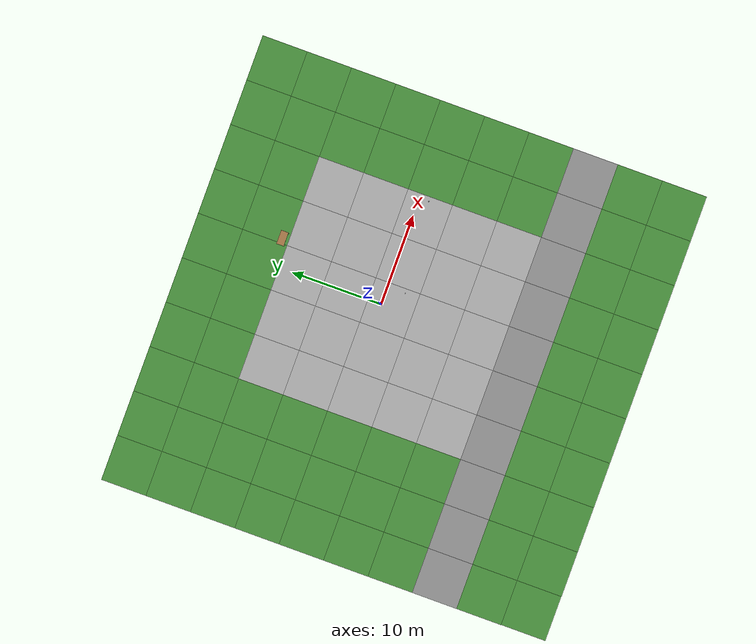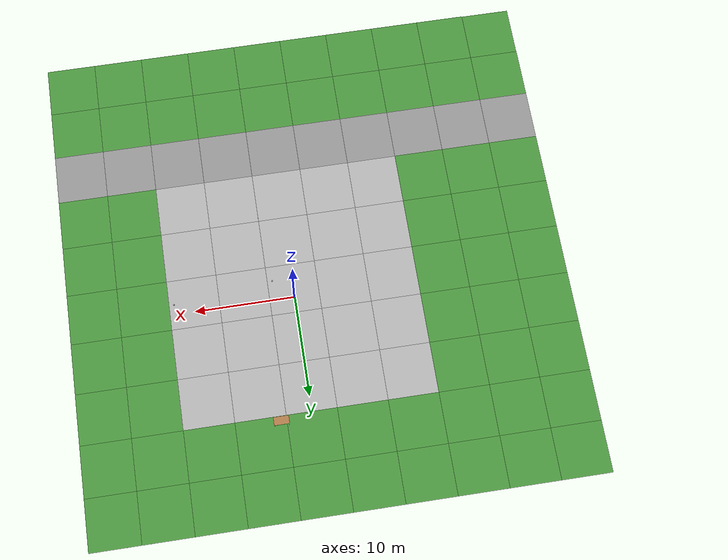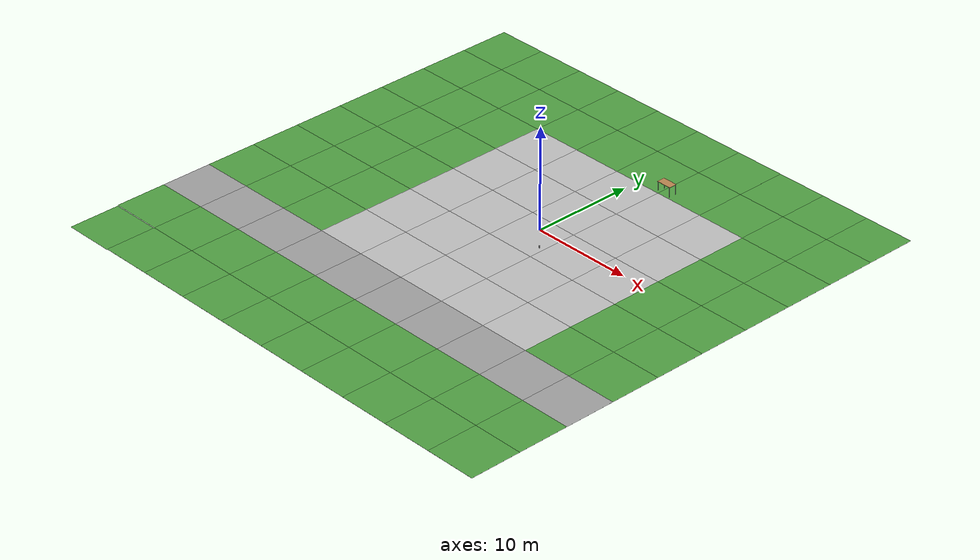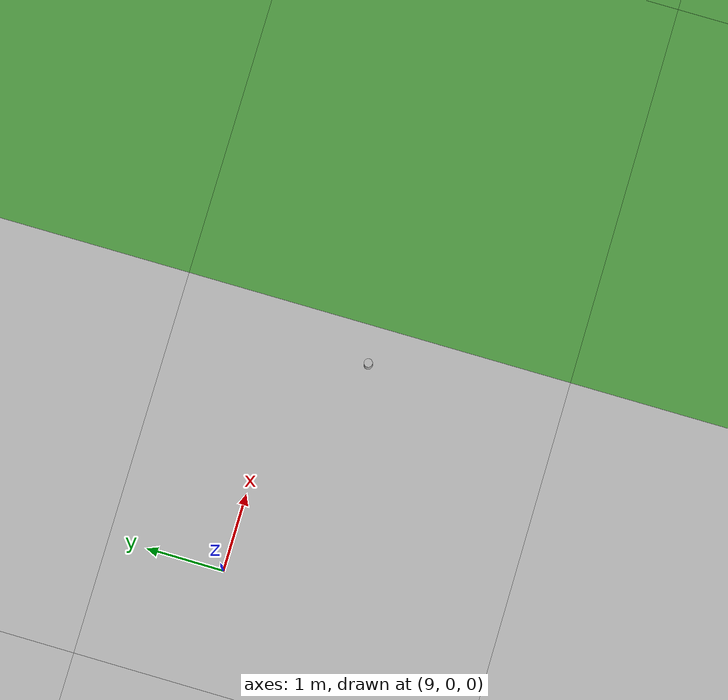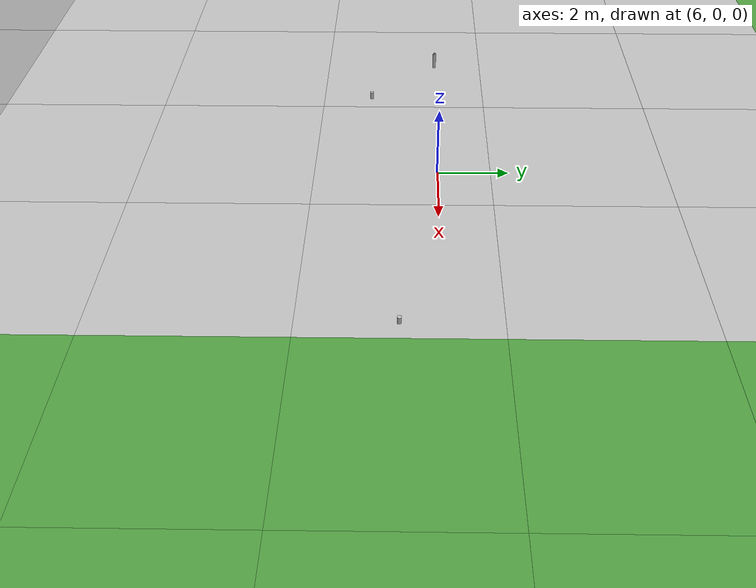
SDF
<sdf version="1.6">
 <world name="myworld">
  <include><uri>model://CropWithWeed</uri><name>Crop_with_weed</name><pose>2 -2 0   0 0 0</pose></include>
  <light name="sun" type="directional">
   <pose>0 0 10 0 -0 0</pose>
   <diffuse>0.8 0.8 0.8 1</diffuse>
   <specular>0.2 0.2 0.2 1</specular>
   <attenuation>
    <range>1000</range>
    <constant>0.9</constant>
    <linear>0.01</linear>
    <quadratic>0.001</quadratic>
   </attenuation>
   <direction>-0.5 0.1 -0.9</direction>
  </light>
  <model name="farm_field_0_0">
   <static>1</static>
   <link name="link">
    <collision name="collision">
     <geometry><plane><normal>0 0 1</normal><size>50 50</size></plane></geometry>
     <surface><friction><ode><mu>100</mu><mu2>50</mu2></ode></friction></surface>
    </collision>
    <visual name="visual_0">
     <pose>-25 -25 0 0 -0 0</pose>
     <cast_shadows>0</cast_shadows>
     <geometry><plane><normal>0 0 1</normal><size>5 5</size></plane></geometry>
     <material>
      <script>
       <uri>model://grass_plane/materials/scripts</uri>
       <uri>model://grass_plane/materials/textures</uri>
       <name>vrc/grass</name>
      </script>
     </material>
    </visual>
    <visual name="visual_1">
     <pose>-20 -25 0 0 -0 0</pose>
     <cast_shadows>0</cast_shadows>
     <geometry><plane><normal>0 0 1</normal><size>5 5</size></plane></geometry>
     <material>
      <script>
       <uri>model://grass_plane/materials/scripts</uri>
       <uri>model://grass_plane/materials/textures</uri>
       <name>vrc/grass</name>
      </script>
     </material>
    </visual>
    <visual name="visual_2">
     <pose>-15 -25 0 0 -0 0</pose>
     <cast_shadows>0</cast_shadows>
     <geometry><plane><normal>0 0 1</normal><size>5 5</size></plane></geometry>
     <material>
      <script>
       <uri>model://grass_plane/materials/scripts</uri>
       <uri>model://grass_plane/materials/textures</uri>
       <name>vrc/grass</name>
      </script>
     </material>
    </visual>
    <visual name="visual_3">
     <pose>-10 -25 0 0 -0 0</pose>
     <cast_shadows>0</cast_shadows>
     <geometry><plane><normal>0 0 1</normal><size>5 5</size></plane></geometry>
     <material>
      <script>
       <uri>model://grass_plane/materials/scripts</uri>
       <uri>model://grass_plane/materials/textures</uri>
       <name>vrc/grass</name>
      </script>
     </material>
    </visual>
    <visual name="visual_4">
     <pose>-5 -25 0 0 -0 0</pose>
     <cast_shadows>0</cast_shadows>
     <geometry><plane><normal>0 0 1</normal><size>5 5</size></plane></geometry>
     <material>
      <script>
       <uri>model://grass_plane/materials/scripts</uri>
       <uri>model://grass_plane/materials/textures</uri>
       <name>vrc/grass</name>
      </script>
     </material>
    </visual>
    <visual name="visual_5">
     <pose>0 -25 0 0 -0 0</pose>
     <cast_shadows>0</cast_shadows>
     <geometry><plane><normal>0 0 1</normal><size>5 5</size></plane></geometry>
     <material>
      <script>
       <uri>model://grass_plane/materials/scripts</uri>
       <uri>model://grass_plane/materials/textures</uri>
       <name>vrc/grass</name>
      </script>
     </material>
    </visual>
    <visual name="visual_6">
     <pose>5 -25 0 0 -0 0</pose>
     <cast_shadows>0</cast_shadows>
     <geometry><plane><normal>0 0 1</normal><size>5 5</size></plane></geometry>
     <material>
      <script>
       <uri>model://grass_plane/materials/scripts</uri>
       <uri>model://grass_plane/materials/textures</uri>
       <name>vrc/grass</name>
      </script>
     </material>
    </visual>
    <visual name="visual_7">
     <pose>10 -25 0 0 -0 0</pose>
     <cast_shadows>0</cast_shadows>
     <geometry><plane><normal>0 0 1</normal><size>5 5</size></plane></geometry>
     <material>
      <script>
       <uri>model://grass_plane/materials/scripts</uri>
       <uri>model://grass_plane/materials/textures</uri>
       <name>vrc/grass</name>
      </script>
     </material>
    </visual>
    <visual name="visual_8">
     <pose>15 -25 0 0 -0 0</pose>
     <cast_shadows>0</cast_shadows>
     <geometry><plane><normal>0 0 1</normal><size>5 5</size></plane></geometry>
     <material>
      <script>
       <uri>model://grass_plane/materials/scripts</uri>
       <uri>model://grass_plane/materials/textures</uri>
       <name>vrc/grass</name>
      </script>
     </material>
    </visual>
    <visual name="visual_9">
     <pose>20 -25 0 0 -0 0</pose>
     <cast_shadows>0</cast_shadows>
     <geometry><plane><normal>0 0 1</normal><size>5 5</size></plane></geometry>
     <material>
      <script>
       <uri>model://grass_plane/materials/scripts</uri>
       <uri>model://grass_plane/materials/textures</uri>
       <name>vrc/grass</name>
      </script>
     </material>
    </visual>
    <visual name="visual_10">
     <pose>-25 -20 0 0 -0 0</pose>
     <cast_shadows>0</cast_shadows>
     <geometry><plane><normal>0 0 1</normal><size>5 5</size></plane></geometry>
     <material>
      <script>
       <uri>model://grass_plane/materials/scripts</uri>
       <uri>model://grass_plane/materials/textures</uri>
       <name>vrc/grass</name>
      </script>
     </material>
    </visual>
    <visual name="visual_11">
     <pose>-20 -20 0 0 -0 0</pose>
     <cast_shadows>0</cast_shadows>
     <geometry><plane><normal>0 0 1</normal><size>5 5</size></plane></geometry>
     <material>
      <script>
       <uri>model://grass_plane/materials/scripts</uri>
       <uri>model://grass_plane/materials/textures</uri>
       <name>vrc/grass</name>
      </script>
     </material>
    </visual>
    <visual name="visual_12">
     <pose>-15 -20 0 0 -0 0</pose>
     <cast_shadows>0</cast_shadows>
     <geometry><plane><normal>0 0 1</normal><size>5 5</size></plane></geometry>
     <material>
      <script>
       <uri>model://grass_plane/materials/scripts</uri>
       <uri>model://grass_plane/materials/textures</uri>
       <name>vrc/grass</name>
      </script>
     </material>
    </visual>
    <visual name="visual_13">
     <pose>-10 -20 0 0 -0 0</pose>
     <cast_shadows>0</cast_shadows>
     <geometry><plane><normal>0 0 1</normal><size>5 5</size></plane></geometry>
     <material>
      <script>
       <uri>model://grass_plane/materials/scripts</uri>
       <uri>model://grass_plane/materials/textures</uri>
       <name>vrc/grass</name>
      </script>
     </material>
    </visual>
    <visual name="visual_14">
     <pose>-5 -20 0 0 -0 0</pose>
     <cast_shadows>0</cast_shadows>
     <geometry><plane><normal>0 0 1</normal><size>5 5</size></plane></geometry>
     <material>
      <script>
       <uri>model://grass_plane/materials/scripts</uri>
       <uri>model://grass_plane/materials/textures</uri>
       <name>vrc/grass</name>
      </script>
     </material>
    </visual>
    <visual name="visual_15">
     <pose>0 -20 0 0 -0 0</pose>
     <cast_shadows>0</cast_shadows>
     <geometry><plane><normal>0 0 1</normal><size>5 5</size></plane></geometry>
     <material>
      <script>
       <uri>model://grass_plane/materials/scripts</uri>
       <uri>model://grass_plane/materials/textures</uri>
       <name>vrc/grass</name>
      </script>
     </material>
    </visual>
    <visual name="visual_16">
     <pose>5 -20 0 0 -0 0</pose>
     <cast_shadows>0</cast_shadows>
     <geometry><plane><normal>0 0 1</normal><size>5 5</size></plane></geometry>
     <material>
      <script>
       <uri>model://grass_plane/materials/scripts</uri>
       <uri>model://grass_plane/materials/textures</uri>
       <name>vrc/grass</name>
      </script>
     </material>
    </visual>
    <visual name="visual_17">
     <pose>10 -20 0 0 -0 0</pose>
     <cast_shadows>0</cast_shadows>
     <geometry><plane><normal>0 0 1</normal><size>5 5</size></plane></geometry>
     <material>
      <script>
       <uri>model://grass_plane/materials/scripts</uri>
       <uri>model://grass_plane/materials/textures</uri>
       <name>vrc/grass</name>
      </script>
     </material>
    </visual>
    <visual name="visual_18">
     <pose>15 -20 0 0 -0 0</pose>
     <cast_shadows>0</cast_shadows>
     <geometry><plane><normal>0 0 1</normal><size>5 5</size></plane></geometry>
     <material>
      <script>
       <uri>model://grass_plane/materials/scripts</uri>
       <uri>model://grass_plane/materials/textures</uri>
       <name>vrc/grass</name>
      </script>
     </material>
    </visual>
    <visual name="visual_19">
     <pose>20 -20 0 0 -0 0</pose>
     <cast_shadows>0</cast_shadows>
     <geometry><plane><normal>0 0 1</normal><size>5 5</size></plane></geometry>
     <material>
      <script>
       <uri>model://grass_plane/materials/scripts</uri>
       <uri>model://grass_plane/materials/textures</uri>
       <name>vrc/grass</name>
      </script>
     </material>
    </visual>
    <visual name="visual_20">
     <pose>-25 -15 0 0 -0 0</pose>
     <cast_shadows>0</cast_shadows>
     <geometry><plane><normal>0 0 1</normal><size>5 5</size></plane></geometry>
     <material>
      <script><uri>file://media/materials/scripts/gazebo.material</uri><name>Gazebo/Grey</name></script>
     </material>
    </visual>
    <visual name="visual_21">
     <pose>-20 -15 0 0 -0 0</pose>
     <cast_shadows>0</cast_shadows>
     <geometry><plane><normal>0 0 1</normal><size>5 5</size></plane></geometry>
     <material>
      <script><uri>file://media/materials/scripts/gazebo.material</uri><name>Gazebo/Grey</name></script>
     </material>
    </visual>
    <visual name="visual_22">
     <pose>-15 -15 0 0 -0 0</pose>
     <cast_shadows>0</cast_shadows>
     <geometry><plane><normal>0 0 1</normal><size>5 5</size></plane></geometry>
     <material>
      <script><uri>file://media/materials/scripts/gazebo.material</uri><name>Gazebo/Grey</name></script>
     </material>
    </visual>
    <visual name="visual_23">
     <pose>-10 -15 0 0 -0 0</pose>
     <cast_shadows>0</cast_shadows>
     <geometry><plane><normal>0 0 1</normal><size>5 5</size></plane></geometry>
     <material>
      <script><uri>file://media/materials/scripts/gazebo.material</uri><name>Gazebo/Grey</name></script>
     </material>
    </visual>
    <visual name="visual_24">
     <pose>-5 -15 0 0 -0 0</pose>
     <cast_shadows>0</cast_shadows>
     <geometry><plane><normal>0 0 1</normal><size>5 5</size></plane></geometry>
     <material>
      <script><uri>file://media/materials/scripts/gazebo.material</uri><name>Gazebo/Grey</name></script>
     </material>
    </visual>
    <visual name="visual_25">
     <pose>0 -15 0 0 -0 0</pose>
     <cast_shadows>0</cast_shadows>
     <geometry><plane><normal>0 0 1</normal><size>5 5</size></plane></geometry>
     <material>
      <script><uri>file://media/materials/scripts/gazebo.material</uri><name>Gazebo/Grey</name></script>
     </material>
    </visual>
    <visual name="visual_26">
     <pose>5 -15 0 0 -0 0</pose>
     <cast_shadows>0</cast_shadows>
     <geometry><plane><normal>0 0 1</normal><size>5 5</size></plane></geometry>
     <material>
      <script><uri>file://media/materials/scripts/gazebo.material</uri><name>Gazebo/Grey</name></script>
     </material>
    </visual>
    <visual name="visual_27">
     <pose>10 -15 0 0 -0 0</pose>
     <cast_shadows>0</cast_shadows>
     <geometry><plane><normal>0 0 1</normal><size>5 5</size></plane></geometry>
     <material>
      <script><uri>file://media/materials/scripts/gazebo.material</uri><name>Gazebo/Grey</name></script>
     </material>
    </visual>
    <visual name="visual_28">
     <pose>15 -15 0 0 -0 0</pose>
     <cast_shadows>0</cast_shadows>
     <geometry><plane><normal>0 0 1</normal><size>5 5</size></plane></geometry>
     <material>
      <script><uri>file://media/materials/scripts/gazebo.material</uri><name>Gazebo/Grey</name></script>
     </material>
    </visual>
    <visual name="visual_29">
     <pose>20 -15 0 0 -0 0</pose>
     <cast_shadows>0</cast_shadows>
     <geometry><plane><normal>0 0 1</normal><size>5 5</size></plane></geometry>
     <material>
      <script><uri>file://media/materials/scripts/gazebo.material</uri><name>Gazebo/Grey</name></script>
     </material>
    </visual>
    <visual name="visual_30">
     <pose>-25 -10 0 0 -0 0</pose>
     <cast_shadows>0</cast_shadows>
     <geometry><plane><normal>0 0 1</normal><size>5 5</size></plane></geometry>
     <material>
      <script>
       <uri>model://grass_plane/materials/scripts</uri>
       <uri>model://grass_plane/materials/textures</uri>
       <name>vrc/grass</name>
      </script>
     </material>
    </visual>
    <visual name="visual_31">
     <pose>-20 -10 0 0 -0 0</pose>
     <cast_shadows>0</cast_shadows>
     <geometry><plane><normal>0 0 1</normal><size>5 5</size></plane></geometry>
     <material>
      <script>
       <uri>model://grass_plane/materials/scripts</uri>
       <uri>model://grass_plane/materials/textures</uri>
       <name>vrc/grass</name>
      </script>
     </material>
    </visual>
    <visual name="visual_32">
     <pose>-15 -10 0 0 -0 0</pose>
     <cast_shadows>0</cast_shadows>
     <geometry><plane><normal>0 0 1</normal><size>5 5</size></plane></geometry>
     <material>
      <script>
       <uri>model://grass_plane/materials/scripts</uri>
       <uri>model://grass_plane/materials/textures</uri>
       <name>vrc/grass</name>
      </script>
     </material>
    </visual>
    <visual name="visual_33">
     <pose>-10 -10 0 0 -0 0</pose>
     <cast_shadows>0</cast_shadows>
     <geometry><plane><normal>0 0 1</normal><size>5 5</size></plane></geometry>
     <material>
      <script>
       <uri>model://pavement_plane/materials/scripts</uri>
       <uri>model://pavement_plane/materials/textures</uri>
       <name>vrc/pavement</name>
      </script>
     </material>
    </visual>
    <visual name="visual_34">
     <pose>-5 -10 0 0 -0 0</pose>
     <cast_shadows>0</cast_shadows>
     <geometry><plane><normal>0 0 1</normal><size>5 5</size></plane></geometry>
     <material>
      <script>
       <uri>model://pavement_plane/materials/scripts</uri>
       <uri>model://pavement_plane/materials/textures</uri>
       <name>vrc/pavement</name>
      </script>
     </material>
    </visual>
    <visual name="visual_35">
     <pose>0 -10 0 0 -0 0</pose>
     <cast_shadows>0</cast_shadows>
     <geometry><plane><normal>0 0 1</normal><size>5 5</size></plane></geometry>
     <material>
      <script>
       <uri>model://pavement_plane/materials/scripts</uri>
       <uri>model://pavement_plane/materials/textures</uri>
       <name>vrc/pavement</name>
      </script>
     </material>
    </visual>
    <visual name="visual_36">
     <pose>5 -10 0 0 -0 0</pose>
     <cast_shadows>0</cast_shadows>
     <geometry><plane><normal>0 0 1</normal><size>5 5</size></plane></geometry>
     <material>
      <script>
       <uri>model://pavement_plane/materials/scripts</uri>
       <uri>model://pavement_plane/materials/textures</uri>
       <name>vrc/pavement</name>
      </script>
     </material>
    </visual>
    <visual name="visual_37">
     <pose>10 -10 0 0 -0 0</pose>
     <cast_shadows>0</cast_shadows>
     <geometry><plane><normal>0 0 1</normal><size>5 5</size></plane></geometry>
     <material>
      <script>
       <uri>model://pavement_plane/materials/scripts</uri>
       <uri>model://pavement_plane/materials/textures</uri>
       <name>vrc/pavement</name>
      </script>
     </material>
    </visual>
    <visual name="visual_38">
     <pose>15 -10 0 0 -0 0</pose>
     <cast_shadows>0</cast_shadows>
     <geometry><plane><normal>0 0 1</normal><size>5 5</size></plane></geometry>
     <material>
      <script>
       <uri>model://grass_plane/materials/scripts</uri>
       <uri>model://grass_plane/materials/textures</uri>
       <name>vrc/grass</name>
      </script>
     </material>
    </visual>
    <visual name="visual_39">
     <pose>20 -10 0 0 -0 0</pose>
     <cast_shadows>0</cast_shadows>
     <geometry><plane><normal>0 0 1</normal><size>5 5</size></plane></geometry>
     <material>
      <script>
       <uri>model://grass_plane/materials/scripts</uri>
       <uri>model://grass_plane/materials/textures</uri>
       <name>vrc/grass</name>
      </script>
     </material>
    </visual>
    <visual name="visual_40">
     <pose>-25 -5 0 0 -0 0</pose>
     <cast_shadows>0</cast_shadows>
     <geometry><plane><normal>0 0 1</normal><size>5 5</size></plane></geometry>
     <material>
      <script>
       <uri>model://grass_plane/materials/scripts</uri>
       <uri>model://grass_plane/materials/textures</uri>
       <name>vrc/grass</name>
      </script>
     </material>
    </visual>
    <visual name="visual_41">
     <pose>-20 -5 0 0 -0 0</pose>
     <cast_shadows>0</cast_shadows>
     <geometry><plane><normal>0 0 1</normal><size>5 5</size></plane></geometry>
     <material>
      <script>
       <uri>model://grass_plane/materials/scripts</uri>
       <uri>model://grass_plane/materials/textures</uri>
       <name>vrc/grass</name>
      </script>
     </material>
    </visual>
    <visual name="visual_42">
     <pose>-15 -5 0 0 -0 0</pose>
     <cast_shadows>0</cast_shadows>
     <geometry><plane><normal>0 0 1</normal><size>5 5</size></plane></geometry>
     <material>
      <script>
       <uri>model://grass_plane/materials/scripts</uri>
       <uri>model://grass_plane/materials/textures</uri>
       <name>vrc/grass</name>
      </script>
     </material>
    </visual>
    <visual name="visual_43">
     <pose>-10 -5 0 0 -0 0</pose>
     <cast_shadows>0</cast_shadows>
     <geometry><plane><normal>0 0 1</normal><size>5 5</size></plane></geometry>
     <material>
      <script>
       <uri>model://pavement_plane/materials/scripts</uri>
       <uri>model://pavement_plane/materials/textures</uri>
       <name>vrc/pavement</name>
      </script>
     </material>
    </visual>
    <visual name="visual_44">
     <pose>-5 -5 0 0 -0 0</pose>
     <cast_shadows>0</cast_shadows>
     <geometry><plane><normal>0 0 1</normal><size>5 5</size></plane></geometry>
     <material>
      <script>
       <uri>model://pavement_plane/materials/scripts</uri>
       <uri>model://pavement_plane/materials/textures</uri>
       <name>vrc/pavement</name>
      </script>
     </material>
    </visual>
    <visual name="visual_45">
     <pose>0 -5 0 0 -0 0</pose>
     <cast_shadows>0</cast_shadows>
     <geometry><plane><normal>0 0 1</normal><size>5 5</size></plane></geometry>
     <material>
      <script>
       <uri>model://pavement_plane/materials/scripts</uri>
       <uri>model://pavement_plane/materials/textures</uri>
       <name>vrc/pavement</name>
      </script>
     </material>
    </visual>
    <visual name="visual_46">
     <pose>5 -5 0 0 -0 0</pose>
     <cast_shadows>0</cast_shadows>
     <geometry><plane><normal>0 0 1</normal><size>5 5</size></plane></geometry>
     <material>
      <script>
       <uri>model://pavement_plane/materials/scripts</uri>
       <uri>model://pavement_plane/materials/textures</uri>
       <name>vrc/pavement</name>
      </script>
     </material>
    </visual>
    <visual name="visual_47">
     <pose>10 -5 0 0 -0 0</pose>
     <cast_shadows>0</cast_shadows>
     <geometry><plane><normal>0 0 1</normal><size>5 5</size></plane></geometry>
     <material>
      <script>
       <uri>model://pavement_plane/materials/scripts</uri>
       <uri>model://pavement_plane/materials/textures</uri>
       <name>vrc/pavement</name>
      </script>
     </material>
    </visual>
    <visual name="visual_48">
     <pose>15 -5 0 0 -0 0</pose>
     <cast_shadows>0</cast_shadows>
     <geometry><plane><normal>0 0 1</normal><size>5 5</size></plane></geometry>
     <material>
      <script>
       <uri>model://grass_plane/materials/scripts</uri>
       <uri>model://grass_plane/materials/textures</uri>
       <name>vrc/grass</name>
      </script>
     </material>
    </visual>
    <visual name="visual_49">
     <pose>20 -5 0 0 -0 0</pose>
     <cast_shadows>0</cast_shadows>
     <geometry><plane><normal>0 0 1</normal><size>5 5</size></plane></geometry>
     <material>
      <script>
       <uri>model://grass_plane/materials/scripts</uri>
       <uri>model://grass_plane/materials/textures</uri>
       <name>vrc/grass</name>
      </script>
     </material>
    </visual>
    <visual name="visual_50">
     <pose>-25 0 0 0 -0 0</pose>
     <cast_shadows>0</cast_shadows>
     <geometry><plane><normal>0 0 1</normal><size>5 5</size></plane></geometry>
     <material>
      <script>
       <uri>model://grass_plane/materials/scripts</uri>
       <uri>model://grass_plane/materials/textures</uri>
       <name>vrc/grass</name>
      </script>
     </material>
    </visual>
    <visual name="visual_51">
     <pose>-20 0 0 0 -0 0</pose>
     <cast_shadows>0</cast_shadows>
     <geometry><plane><normal>0 0 1</normal><size>5 5</size></plane></geometry>
     <material>
      <script>
       <uri>model://grass_plane/materials/scripts</uri>
       <uri>model://grass_plane/materials/textures</uri>
       <name>vrc/grass</name>
      </script>
     </material>
    </visual>
    <visual name="visual_52">
     <pose>-15 0 0 0 -0 0</pose>
     <cast_shadows>0</cast_shadows>
     <geometry><plane><normal>0 0 1</normal><size>5 5</size></plane></geometry>
     <material>
      <script>
       <uri>model://grass_plane/materials/scripts</uri>
       <uri>model://grass_plane/materials/textures</uri>
       <name>vrc/grass</name>
      </script>
     </material>
    </visual>
    <visual name="visual_53">
     <pose>-10 0 0 0 -0 0</pose>
     <cast_shadows>0</cast_shadows>
     <geometry><plane><normal>0 0 1</normal><size>5 5</size></plane></geometry>
     <material>
      <script>
       <uri>model://pavement_plane/materials/scripts</uri>
       <uri>model://pavement_plane/materials/textures</uri>
       <name>vrc/pavement</name>
      </script>
     </material>
    </visual>
    <visual name="visual_54">
     <pose>-5 0 0 0 -0 0</pose>
     <cast_shadows>0</cast_shadows>
     <geometry><plane><normal>0 0 1</normal><size>5 5</size></plane></geometry>
     <material>
      <script>
       <uri>model://pavement_plane/materials/scripts</uri>
       <uri>model://pavement_plane/materials/textures</uri>
       <name>vrc/pavement</name>
      </script>
     </material>
    </visual>
    <visual name="visual_55">
     <cast_shadows>0</cast_shadows>
     <geometry><plane><normal>0 0 1</normal><size>5 5</size></plane></geometry>
     <material>
      <script>
       <uri>model://pavement_plane/materials/scripts</uri>
       <uri>model://pavement_plane/materials/textures</uri>
       <name>vrc/pavement</name>
      </script>
     </material>
    </visual>
    <visual name="visual_56">
     <pose>5 0 0 0 -0 0</pose>
     <cast_shadows>0</cast_shadows>
     <geometry><plane><normal>0 0 1</normal><size>5 5</size></plane></geometry>
     <material>
      <script>
       <uri>model://pavement_plane/materials/scripts</uri>
       <uri>model://pavement_plane/materials/textures</uri>
       <name>vrc/pavement</name>
      </script>
     </material>
    </visual>
    <visual name="visual_57">
     <pose>10 0 0 0 -0 0</pose>
     <cast_shadows>0</cast_shadows>
     <geometry><plane><normal>0 0 1</normal><size>5 5</size></plane></geometry>
     <material>
      <script>
       <uri>model://pavement_plane/materials/scripts</uri>
       <uri>model://pavement_plane/materials/textures</uri>
       <name>vrc/pavement</name>
      </script>
     </material>
    </visual>
    <visual name="visual_58">
     <pose>15 0 0 0 -0 0</pose>
     <cast_shadows>0</cast_shadows>
     <geometry><plane><normal>0 0 1</normal><size>5 5</size></plane></geometry>
     <material>
      <script>
       <uri>model://grass_plane/materials/scripts</uri>
       <uri>model://grass_plane/materials/textures</uri>
       <name>vrc/grass</name>
      </script>
     </material>
    </visual>
    <visual name="visual_59">
     <pose>20 0 0 0 -0 0</pose>
     <cast_shadows>0</cast_shadows>
     <geometry><plane><normal>0 0 1</normal><size>5 5</size></plane></geometry>
     <material>
      <script>
       <uri>model://grass_plane/materials/scripts</uri>
       <uri>model://grass_plane/materials/textures</uri>
       <name>vrc/grass</name>
      </script>
     </material>
    </visual>
    <visual name="visual_60">
     <pose>-25 5 0 0 -0 0</pose>
     <cast_shadows>0</cast_shadows>
     <geometry><plane><normal>0 0 1</normal><size>5 5</size></plane></geometry>
     <material>
      <script>
       <uri>model://grass_plane/materials/scripts</uri>
       <uri>model://grass_plane/materials/textures</uri>
       <name>vrc/grass</name>
      </script>
     </material>
    </visual>
    <visual name="visual_61">
     <pose>-20 5 0 0 -0 0</pose>
     <cast_shadows>0</cast_shadows>
     <geometry><plane><normal>0 0 1</normal><size>5 5</size></plane></geometry>
     <material>
      <script>
       <uri>model://grass_plane/materials/scripts</uri>
       <uri>model://grass_plane/materials/textures</uri>
       <name>vrc/grass</name>
      </script>
     </material>
    </visual>
    <visual name="visual_62">
     <pose>-15 5 0 0 -0 0</pose>
     <cast_shadows>0</cast_shadows>
     <geometry><plane><normal>0 0 1</normal><size>5 5</size></plane></geometry>
     <material>
      <script>
       <uri>model://grass_plane/materials/scripts</uri>
       <uri>model://grass_plane/materials/textures</uri>
       <name>vrc/grass</name>
      </script>
     </material>
    </visual>
    <visual name="visual_63">
     <pose>-10 5 0 0 -0 0</pose>
     <cast_shadows>0</cast_shadows>
     <geometry><plane><normal>0 0 1</normal><size>5 5</size></plane></geometry>
     <material>
      <script>
       <uri>model://pavement_plane/materials/scripts</uri>
       <uri>model://pavement_plane/materials/textures</uri>
       <name>vrc/pavement</name>
      </script>
     </material>
    </visual>
    <visual name="visual_64">
     <pose>-5 5 0 0 -0 0</pose>
     <cast_shadows>0</cast_shadows>
     <geometry><plane><normal>0 0 1</normal><size>5 5</size></plane></geometry>
     <material>
      <script>
       <uri>model://pavement_plane/materials/scripts</uri>
       <uri>model://pavement_plane/materials/textures</uri>
       <name>vrc/pavement</name>
      </script>
     </material>
    </visual>
    <visual name="visual_65">
     <pose>0 5 0 0 -0 0</pose>
     <cast_shadows>0</cast_shadows>
     <geometry><plane><normal>0 0 1</normal><size>5 5</size></plane></geometry>
     <material>
      <script>
       <uri>model://pavement_plane/materials/scripts</uri>
       <uri>model://pavement_plane/materials/textures</uri>
       <name>vrc/pavement</name>
      </script>
     </material>
    </visual>
    <visual name="visual_66">
     <pose>5 5 0 0 -0 0</pose>
     <cast_shadows>0</cast_shadows>
     <geometry><plane><normal>0 0 1</normal><size>5 5</size></plane></geometry>
     <material>
      <script>
       <uri>model://pavement_plane/materials/scripts</uri>
       <uri>model://pavement_plane/materials/textures</uri>
       <name>vrc/pavement</name>
      </script>
     </material>
    </visual>
    <visual name="visual_67">
     <pose>10 5 0 0 -0 0</pose>
     <cast_shadows>0</cast_shadows>
     <geometry><plane><normal>0 0 1</normal><size>5 5</size></plane></geometry>
     <material>
      <script>
       <uri>model://pavement_plane/materials/scripts</uri>
       <uri>model://pavement_plane/materials/textures</uri>
       <name>vrc/pavement</name>
      </script>
     </material>
    </visual>
    <visual name="visual_68">
     <pose>15 5 0 0 -0 0</pose>
     <cast_shadows>0</cast_shadows>
     <geometry><plane><normal>0 0 1</normal><size>5 5</size></plane></geometry>
     <material>
      <script>
       <uri>model://grass_plane/materials/scripts</uri>
       <uri>model://grass_plane/materials/textures</uri>
       <name>vrc/grass</name>
      </script>
     </material>
    </visual>
    <visual name="visual_69">
     <pose>20 5 0 0 -0 0</pose>
     <cast_shadows>0</cast_shadows>
     <geometry><plane><normal>0 0 1</normal><size>5 5</size></plane></geometry>
     <material>
      <script>
       <uri>model://grass_plane/materials/scripts</uri>
       <uri>model://grass_plane/materials/textures</uri>
       <name>vrc/grass</name>
      </script>
     </material>
    </visual>
    <visual name="visual_70">
     <pose>-25 10 0 0 -0 0</pose>
     <cast_shadows>0</cast_shadows>
     <geometry><plane><normal>0 0 1</normal><size>5 5</size></plane></geometry>
     <material>
      <script>
       <uri>model://grass_plane/materials/scripts</uri>
       <uri>model://grass_plane/materials/textures</uri>
       <name>vrc/grass</name>
      </script>
     </material>
    </visual>
    <visual name="visual_71">
     <pose>-20 10 0 0 -0 0</pose>
     <cast_shadows>0</cast_shadows>
     <geometry><plane><normal>0 0 1</normal><size>5 5</size></plane></geometry>
     <material>
      <script>
       <uri>model://grass_plane/materials/scripts</uri>
       <uri>model://grass_plane/materials/textures</uri>
       <name>vrc/grass</name>
      </script>
     </material>
    </visual>
    <visual name="visual_72">
     <pose>-15 10 0 0 -0 0</pose>
     <cast_shadows>0</cast_shadows>
     <geometry><plane><normal>0 0 1</normal><size>5 5</size></plane></geometry>
     <material>
      <script>
       <uri>model://grass_plane/materials/scripts</uri>
       <uri>model://grass_plane/materials/textures</uri>
       <name>vrc/grass</name>
      </script>
     </material>
    </visual>
    <visual name="visual_73">
     <pose>-10 10 0 0 -0 0</pose>
     <cast_shadows>0</cast_shadows>
     <geometry><plane><normal>0 0 1</normal><size>5 5</size></plane></geometry>
     <material>
      <script>
       <uri>model://pavement_plane/materials/scripts</uri>
       <uri>model://pavement_plane/materials/textures</uri>
       <name>vrc/pavement</name>
      </script>
     </material>
    </visual>
    <visual name="visual_74">
     <pose>-5 10 0 0 -0 0</pose>
     <cast_shadows>0</cast_shadows>
     <geometry><plane><normal>0 0 1</normal><size>5 5</size></plane></geometry>
     <material>
      <script>
       <uri>model://pavement_plane/materials/scripts</uri>
       <uri>model://pavement_plane/materials/textures</uri>
       <name>vrc/pavement</name>
      </script>
     </material>
    </visual>
    <visual name="visual_75">
     <pose>0 10 0 0 -0 0</pose>
     <cast_shadows>0</cast_shadows>
     <geometry><plane><normal>0 0 1</normal><size>5 5</size></plane></geometry>
     <material>
      <script>
       <uri>model://pavement_plane/materials/scripts</uri>
       <uri>model://pavement_plane/materials/textures</uri>
       <name>vrc/pavement</name>
      </script>
     </material>
    </visual>
    <visual name="visual_76">
     <pose>5 10 0 0 -0 0</pose>
     <cast_shadows>0</cast_shadows>
     <geometry><plane><normal>0 0 1</normal><size>5 5</size></plane></geometry>
     <material>
      <script>
       <uri>model://pavement_plane/materials/scripts</uri>
       <uri>model://pavement_plane/materials/textures</uri>
       <name>vrc/pavement</name>
      </script>
     </material>
    </visual>
    <visual name="visual_77">
     <pose>10 10 0 0 -0 0</pose>
     <cast_shadows>0</cast_shadows>
     <geometry><plane><normal>0 0 1</normal><size>5 5</size></plane></geometry>
     <material>
      <script>
       <uri>model://pavement_plane/materials/scripts</uri>
       <uri>model://pavement_plane/materials/textures</uri>
       <name>vrc/pavement</name>
      </script>
     </material>
    </visual>
    <visual name="visual_78">
     <pose>15 10 0 0 -0 0</pose>
     <cast_shadows>0</cast_shadows>
     <geometry><plane><normal>0 0 1</normal><size>5 5</size></plane></geometry>
     <material>
      <script>
       <uri>model://grass_plane/materials/scripts</uri>
       <uri>model://grass_plane/materials/textures</uri>
       <name>vrc/grass</name>
      </script>
     </material>
    </visual>
    <visual name="visual_79">
     <pose>20 10 0 0 -0 0</pose>
     <cast_shadows>0</cast_shadows>
     <geometry><plane><normal>0 0 1</normal><size>5 5</size></plane></geometry>
     <material>
      <script>
       <uri>model://grass_plane/materials/scripts</uri>
       <uri>model://grass_plane/materials/textures</uri>
       <name>vrc/grass</name>
      </script>
     </material>
    </visual>
    <visual name="visual_80">
     <pose>-25 15 0 0 -0 0</pose>
     <cast_shadows>0</cast_shadows>
     <geometry><plane><normal>0 0 1</normal><size>5 5</size></plane></geometry>
     <material>
      <script>
       <uri>model://grass_plane/materials/scripts</uri>
       <uri>model://grass_plane/materials/textures</uri>
       <name>vrc/grass</name>
      </script>
     </material>
    </visual>
    <visual name="visual_81">
     <pose>-20 15 0 0 -0 0</pose>
     <cast_shadows>0</cast_shadows>
     <geometry><plane><normal>0 0 1</normal><size>5 5</size></plane></geometry>
     <material>
      <script>
       <uri>model://grass_plane/materials/scripts</uri>
       <uri>model://grass_plane/materials/textures</uri>
       <name>vrc/grass</name>
      </script>
     </material>
    </visual>
    <visual name="visual_82">
     <pose>-15 15 0 0 -0 0</pose>
     <cast_shadows>0</cast_shadows>
     <geometry><plane><normal>0 0 1</normal><size>5 5</size></plane></geometry>
     <material>
      <script>
       <uri>model://grass_plane/materials/scripts</uri>
       <uri>model://grass_plane/materials/textures</uri>
       <name>vrc/grass</name>
      </script>
     </material>
    </visual>
    <visual name="visual_83">
     <pose>-10 15 0 0 -0 0</pose>
     <cast_shadows>0</cast_shadows>
     <geometry><plane><normal>0 0 1</normal><size>5 5</size></plane></geometry>
     <material>
      <script>
       <uri>model://grass_plane/materials/scripts</uri>
       <uri>model://grass_plane/materials/textures</uri>
       <name>vrc/grass</name>
      </script>
     </material>
    </visual>
    <visual name="visual_84">
     <pose>-5 15 0 0 -0 0</pose>
     <cast_shadows>0</cast_shadows>
     <geometry><plane><normal>0 0 1</normal><size>5 5</size></plane></geometry>
     <material>
      <script>
       <uri>model://grass_plane/materials/scripts</uri>
       <uri>model://grass_plane/materials/textures</uri>
       <name>vrc/grass</name>
      </script>
     </material>
    </visual>
    <visual name="visual_85">
     <pose>0 15 0 0 -0 0</pose>
     <cast_shadows>0</cast_shadows>
     <geometry><plane><normal>0 0 1</normal><size>5 5</size></plane></geometry>
     <material>
      <script>
       <uri>model://grass_plane/materials/scripts</uri>
       <uri>model://grass_plane/materials/textures</uri>
       <name>vrc/grass</name>
      </script>
     </material>
    </visual>
    <visual name="visual_86">
     <pose>5 15 0 0 -0 0</pose>
     <cast_shadows>0</cast_shadows>
     <geometry><plane><normal>0 0 1</normal><size>5 5</size></plane></geometry>
     <material>
      <script>
       <uri>model://grass_plane/materials/scripts</uri>
       <uri>model://grass_plane/materials/textures</uri>
       <name>vrc/grass</name>
      </script>
     </material>
    </visual>
    <visual name="visual_87">
     <pose>10 15 0 0 -0 0</pose>
     <cast_shadows>0</cast_shadows>
     <geometry><plane><normal>0 0 1</normal><size>5 5</size></plane></geometry>
     <material>
      <script>
       <uri>model://grass_plane/materials/scripts</uri>
       <uri>model://grass_plane/materials/textures</uri>
       <name>vrc/grass</name>
      </script>
     </material>
    </visual>
    <visual name="visual_88">
     <pose>15 15 0 0 -0 0</pose>
     <cast_shadows>0</cast_shadows>
     <geometry><plane><normal>0 0 1</normal><size>5 5</size></plane></geometry>
     <material>
      <script>
       <uri>model://grass_plane/materials/scripts</uri>
       <uri>model://grass_plane/materials/textures</uri>
       <name>vrc/grass</name>
      </script>
     </material>
    </visual>
    <visual name="visual_89">
     <pose>20 15 0 0 -0 0</pose>
     <cast_shadows>0</cast_shadows>
     <geometry><plane><normal>0 0 1</normal><size>5 5</size></plane></geometry>
     <material>
      <script>
       <uri>model://grass_plane/materials/scripts</uri>
       <uri>model://grass_plane/materials/textures</uri>
       <name>vrc/grass</name>
      </script>
     </material>
    </visual>
    <visual name="visual_90">
     <pose>-25 20 0 0 -0 0</pose>
     <cast_shadows>0</cast_shadows>
     <geometry><plane><normal>0 0 1</normal><size>5 5</size></plane></geometry>
     <material>
      <script>
       <uri>model://grass_plane/materials/scripts</uri>
       <uri>model://grass_plane/materials/textures</uri>
       <name>vrc/grass</name>
      </script>
     </material>
    </visual>
    <visual name="visual_91">
     <pose>-20 20 0 0 -0 0</pose>
     <cast_shadows>0</cast_shadows>
     <geometry><plane><normal>0 0 1</normal><size>5 5</size></plane></geometry>
     <material>
      <script>
       <uri>model://grass_plane/materials/scripts</uri>
       <uri>model://grass_plane/materials/textures</uri>
       <name>vrc/grass</name>
      </script>
     </material>
    </visual>
    <visual name="visual_92">
     <pose>-15 20 0 0 -0 0</pose>
     <cast_shadows>0</cast_shadows>
     <geometry><plane><normal>0 0 1</normal><size>5 5</size></plane></geometry>
     <material>
      <script>
       <uri>model://grass_plane/materials/scripts</uri>
       <uri>model://grass_plane/materials/textures</uri>
       <name>vrc/grass</name>
      </script>
     </material>
    </visual>
    <visual name="visual_93">
     <pose>-10 20 0 0 -0 0</pose>
     <cast_shadows>0</cast_shadows>
     <geometry><plane><normal>0 0 1</normal><size>5 5</size></plane></geometry>
     <material>
      <script>
       <uri>model://grass_plane/materials/scripts</uri>
       <uri>model://grass_plane/materials/textures</uri>
       <name>vrc/grass</name>
      </script>
     </material>
    </visual>
    <visual name="visual_94">
     <pose>-5 20 0 0 -0 0</pose>
     <cast_shadows>0</cast_shadows>
     <geometry><plane><normal>0 0 1</normal><size>5 5</size></plane></geometry>
     <material>
      <script>
       <uri>model://grass_plane/materials/scripts</uri>
       <uri>model://grass_plane/materials/textures</uri>
       <name>vrc/grass</name>
      </script>
     </material>
    </visual>
    <visual name="visual_95">
     <pose>0 20 0 0 -0 0</pose>
     <cast_shadows>0</cast_shadows>
     <geometry><plane><normal>0 0 1</normal><size>5 5</size></plane></geometry>
     <material>
      <script>
       <uri>model://grass_plane/materials/scripts</uri>
       <uri>model://grass_plane/materials/textures</uri>
       <name>vrc/grass</name>
      </script>
     </material>
    </visual>
    <visual name="visual_96">
     <pose>5 20 0 0 -0 0</pose>
     <cast_shadows>0</cast_shadows>
     <geometry><plane><normal>0 0 1</normal><size>5 5</size></plane></geometry>
     <material>
      <script>
       <uri>model://grass_plane/materials/scripts</uri>
       <uri>model://grass_plane/materials/textures</uri>
       <name>vrc/grass</name>
      </script>
     </material>
    </visual>
    <visual name="visual_97">
     <pose>10 20 0 0 -0 0</pose>
     <cast_shadows>0</cast_shadows>
     <geometry><plane><normal>0 0 1</normal><size>5 5</size></plane></geometry>
     <material>
      <script>
       <uri>model://grass_plane/materials/scripts</uri>
       <uri>model://grass_plane/materials/textures</uri>
       <name>vrc/grass</name>
      </script>
     </material>
    </visual>
    <visual name="visual_98">
     <pose>15 20 0 0 -0 0</pose>
     <cast_shadows>0</cast_shadows>
     <geometry><plane><normal>0 0 1</normal><size>5 5</size></plane></geometry>
     <material>
      <script>
       <uri>model://grass_plane/materials/scripts</uri>
       <uri>model://grass_plane/materials/textures</uri>
       <name>vrc/grass</name>
      </script>
     </material>
    </visual>
    <visual name="visual_99">
     <pose>20 20 0 0 -0 0</pose>
     <cast_shadows>0</cast_shadows>
     <geometry><plane><normal>0 0 1</normal><size>5 5</size></plane></geometry>
     <material>
      <script>
       <uri>model://grass_plane/materials/scripts</uri>
       <uri>model://grass_plane/materials/textures</uri>
       <name>vrc/grass</name>
      </script>
     </material>
    </visual>
   </link>
   <pose>0 -1 0 0 -0 0</pose>
  </model>
  <model name="Crop_with_weed">
   <link name="link">
    <pose>0 0 0.115 0 -0 0</pose>
    <inertial>
     <mass>0.39</mass>
     <inertia><ixx>0.00058</ixx><ixy>0</ixy><ixz>0</ixz><iyy>0.00058</iyy><iyz>0</iyz><izz>0.00019</izz></inertia>
    </inertial>
    <collision name="collision">
     <geometry><cylinder><radius>0.055</radius><length>0.2</length></cylinder></geometry>
    </collision>
    <visual name="visual">
     <geometry><cylinder><radius>0.055</radius><length>0.2</length></cylinder></geometry>
     <material>
      <script>
       <uri>model://CropWithWeed/materials/scripts</uri>
       <uri>model://CropWithWeed/materials/textures</uri>
       <name>CropWithWeed/Diffuse</name>
      </script>
     </material>
    </visual>
   </link>
   <pose>12 -1 -0.015001 0 -0 -4e-06</pose>
  </model>
  <model name="Crop_with_weed">
   <link name="link">
    <pose>0 0 0.115 0 -0 0</pose>
    <inertial>
     <mass>0.39</mass>
     <inertia><ixx>0.00058</ixx><ixy>0</ixy><ixz>0</ixz><iyy>0.00058</iyy><iyz>0</iyz><izz>0.00019</izz></inertia>
    </inertial>
    <collision name="collision">
     <geometry><cylinder><radius>0.055</radius><length>0.2</length></cylinder></geometry>
    </collision>
    <visual name="visual">
     <geometry><cylinder><radius>0.055</radius><length>0.2</length></cylinder></geometry>
     <material>
      <script>
       <uri>model://CropWithWeed/materials/scripts</uri>
       <uri>model://CropWithWeed/materials/textures</uri>
       <name>CropWithWeed/Diffuse</name>
      </script>
     </material>
    </visual>
   </link>
   <pose>12 -1 -0.015001 0 -0 -4e-06</pose>
  </model>
  <model name="Crop_with_weed">
   <link name="link">
    <pose>0 0 0.115 0 -0 0</pose>
    <inertial>
     <mass>0.39</mass>
     <inertia><ixx>0.00058</ixx><ixy>0</ixy><ixz>0</ixz><iyy>0.00058</iyy><iyz>0</iyz><izz>0.00019</izz></inertia>
    </inertial>
    <collision name="collision">
     <geometry><cylinder><radius>0.055</radius><length>0.2</length></cylinder></geometry>
    </collision>
    <visual name="visual">
     <geometry><cylinder><radius>0.055</radius><length>0.2</length></cylinder></geometry>
     <material>
      <script>
       <uri>model://CropWithWeed/materials/scripts</uri>
       <uri>model://CropWithWeed/materials/textures</uri>
       <name>CropWithWeed/Diffuse</name>
      </script>
     </material>
    </visual>
   </link>
   <pose>12 -1 -0.015001 0 -0 -4e-06</pose>
  </model>
  <model name="Crop_with_weed">
   <link name="link">
    <pose>0 0 0.115 0 -0 0</pose>
    <inertial>
     <mass>0.39</mass>
     <inertia><ixx>0.00058</ixx><ixy>0</ixy><ixz>0</ixz><iyy>0.00058</iyy><iyz>0</iyz><izz>0.00019</izz></inertia>
    </inertial>
    <collision name="collision">
     <geometry><cylinder><radius>0.055</radius><length>0.2</length></cylinder></geometry>
    </collision>
    <visual name="visual">
     <geometry><cylinder><radius>0.055</radius><length>0.2</length></cylinder></geometry>
     <material>
      <script>
       <uri>model://CropWithWeed/materials/scripts</uri>
       <uri>model://CropWithWeed/materials/textures</uri>
       <name>CropWithWeed/Diffuse</name>
      </script>
     </material>
    </visual>
   </link>
   <pose>12 -1 -0.015001 0 -0 -4e-06</pose>
  </model>
  <model name="Crop_with_weed">
   <link name="link">
    <pose>0 0 0.115 0 -0 0</pose>
    <inertial>
     <mass>0.39</mass>
     <inertia><ixx>0.00058</ixx><ixy>0</ixy><ixz>0</ixz><iyy>0.00058</iyy><iyz>0</iyz><izz>0.00019</izz></inertia>
    </inertial>
    <collision name="collision">
     <geometry><cylinder><radius>0.055</radius><length>0.2</length></cylinder></geometry>
    </collision>
    <visual name="visual">
     <geometry><cylinder><radius>0.055</radius><length>0.2</length></cylinder></geometry>
     <material>
      <script>
       <uri>model://CropWithWeed/materials/scripts</uri>
       <uri>model://CropWithWeed/materials/textures</uri>
       <name>CropWithWeed/Diffuse</name>
      </script>
     </material>
    </visual>
   </link>
   <pose>12 -1 -0.015001 0 -0 -4e-06</pose>
  </model>
  <model name="Crop_with_weed">
   <link name="link">
    <pose>0 0 0.115 0 -0 0</pose>
    <inertial>
     <mass>0.39</mass>
     <inertia><ixx>0.00058</ixx><ixy>0</ixy><ixz>0</ixz><iyy>0.00058</iyy><iyz>0</iyz><izz>0.00019</izz></inertia>
    </inertial>
    <collision name="collision">
     <geometry><cylinder><radius>0.055</radius><length>0.2</length></cylinder></geometry>
    </collision>
    <visual name="visual">
     <geometry><cylinder><radius>0.055</radius><length>0.2</length></cylinder></geometry>
     <material>
      <script>
       <uri>model://CropWithWeed/materials/scripts</uri>
       <uri>model://CropWithWeed/materials/textures</uri>
       <name>CropWithWeed/Diffuse</name>
      </script>
     </material>
    </visual>
   </link>
   <pose>12 -1 -0.015001 0 -0 -4e-06</pose>
  </model>
  <model name="Crop_with_weed">
   <link name="link">
    <pose>0 0 0.115 0 -0 0</pose>
    <inertial>
     <mass>0.39</mass>
     <inertia><ixx>0.00058</ixx><ixy>0</ixy><ixz>0</ixz><iyy>0.00058</iyy><iyz>0</iyz><izz>0.00019</izz></inertia>
    </inertial>
    <collision name="collision">
     <geometry><cylinder><radius>0.055</radius><length>0.2</length></cylinder></geometry>
    </collision>
    <visual name="visual">
     <geometry><cylinder><radius>0.055</radius><length>0.2</length></cylinder></geometry>
     <material>
      <script>
       <uri>model://CropWithWeed/materials/scripts</uri>
       <uri>model://CropWithWeed/materials/textures</uri>
       <name>CropWithWeed/Diffuse</name>
      </script>
     </material>
    </visual>
   </link>
   <pose>12 -1 -0.015001 0 -0 -4e-06</pose>
  </model>
  <model name="Crop_with_weed">
   <link name="link">
    <pose>0 0 0.115 0 -0 0</pose>
    <inertial>
     <mass>0.39</mass>
     <inertia><ixx>0.00058</ixx><ixy>0</ixy><ixz>0</ixz><iyy>0.00058</iyy><iyz>0</iyz><izz>0.00019</izz></inertia>
    </inertial>
    <collision name="collision">
     <geometry><cylinder><radius>0.055</radius><length>0.2</length></cylinder></geometry>
    </collision>
    <visual name="visual">
     <geometry><cylinder><radius>0.055</radius><length>0.2</length></cylinder></geometry>
     <material>
      <script>
       <uri>model://CropWithWeed/materials/scripts</uri>
       <uri>model://CropWithWeed/materials/textures</uri>
       <name>CropWithWeed/Diffuse</name>
      </script>
     </material>
    </visual>
   </link>
   <pose>12 -1 -0.015001 0 -0 -4e-06</pose>
  </model>
  <model name="Crop_with_weed">
   <link name="link">
    <pose>0 0 0.115 0 -0 0</pose>
    <inertial>
     <mass>0.39</mass>
     <inertia><ixx>0.00058</ixx><ixy>0</ixy><ixz>0</ixz><iyy>0.00058</iyy><iyz>0</iyz><izz>0.00019</izz></inertia>
    </inertial>
    <collision name="collision">
     <geometry><cylinder><radius>0.055</radius><length>0.2</length></cylinder></geometry>
    </collision>
    <visual name="visual">
     <geometry><cylinder><radius>0.055</radius><length>0.2</length></cylinder></geometry>
     <material>
      <script>
       <uri>model://CropWithWeed/materials/scripts</uri>
       <uri>model://CropWithWeed/materials/textures</uri>
       <name>CropWithWeed/Diffuse</name>
      </script>
     </material>
    </visual>
   </link>
   <pose>12 -1 -0.015001 0 -0 -4e-06</pose>
  </model>
  <model name="Crop_with_weed">
   <link name="link">
    <pose>0 0 0.115 0 -0 0</pose>
    <inertial>
     <mass>0.39</mass>
     <inertia><ixx>0.00058</ixx><ixy>0</ixy><ixz>0</ixz><iyy>0.00058</iyy><iyz>0</iyz><izz>0.00019</izz></inertia>
    </inertial>
    <collision name="collision">
     <geometry><cylinder><radius>0.055</radius><length>0.2</length></cylinder></geometry>
    </collision>
    <visual name="visual">
     <geometry><cylinder><radius>0.055</radius><length>0.2</length></cylinder></geometry>
     <material>
      <script>
       <uri>model://CropWithWeed/materials/scripts</uri>
       <uri>model://CropWithWeed/materials/textures</uri>
       <name>CropWithWeed/Diffuse</name>
      </script>
     </material>
    </visual>
   </link>
   <pose>12 -1 -0.015001 0 -0 -4e-06</pose>
  </model>
  <model name="Crop_with_weed">
   <link name="link">
    <pose>0 0 0.115 0 -0 0</pose>
    <inertial>
     <mass>0.39</mass>
     <inertia><ixx>0.00058</ixx><ixy>0</ixy><ixz>0</ixz><iyy>0.00058</iyy><iyz>0</iyz><izz>0.00019</izz></inertia>
    </inertial>
    <collision name="collision">
     <geometry><cylinder><radius>0.055</radius><length>0.2</length></cylinder></geometry>
    </collision>
    <visual name="visual">
     <geometry><cylinder><radius>0.055</radius><length>0.2</length></cylinder></geometry>
     <material>
      <script>
       <uri>model://CropWithWeed/materials/scripts</uri>
       <uri>model://CropWithWeed/materials/textures</uri>
       <name>CropWithWeed/Diffuse</name>
      </script>
     </material>
    </visual>
   </link>
   <pose>12 -1 -0.015001 0 -0 -4e-06</pose>
  </model>
  <model name="Crop_with_weed">
   <link name="link">
    <pose>0 0 0.115 0 -0 0</pose>
    <inertial>
     <mass>0.39</mass>
     <inertia><ixx>0.00058</ixx><ixy>0</ixy><ixz>0</ixz><iyy>0.00058</iyy><iyz>0</iyz><izz>0.00019</izz></inertia>
    </inertial>
    <collision name="collision">
     <geometry><cylinder><radius>0.055</radius><length>0.2</length></cylinder></geometry>
    </collision>
    <visual name="visual">
     <geometry><cylinder><radius>0.055</radius><length>0.2</length></cylinder></geometry>
     <material>
      <script>
       <uri>model://CropWithWeed/materials/scripts</uri>
       <uri>model://CropWithWeed/materials/textures</uri>
       <name>CropWithWeed/Diffuse</name>
      </script>
     </material>
    </visual>
   </link>
   <pose>12 -1 -0.015001 0 -0 -4e-06</pose>
  </model>
  <model name="Crop_with_weed">
   <link name="link">
    <pose>0 0 0.115 0 -0 0</pose>
    <inertial>
     <mass>0.39</mass>
     <inertia><ixx>0.00058</ixx><ixy>0</ixy><ixz>0</ixz><iyy>0.00058</iyy><iyz>0</iyz><izz>0.00019</izz></inertia>
    </inertial>
    <collision name="collision">
     <geometry><cylinder><radius>0.055</radius><length>0.2</length></cylinder></geometry>
    </collision>
    <visual name="visual">
     <geometry><cylinder><radius>0.055</radius><length>0.2</length></cylinder></geometry>
     <material>
      <script>
       <uri>model://CropWithWeed/materials/scripts</uri>
       <uri>model://CropWithWeed/materials/textures</uri>
       <name>CropWithWeed/Diffuse</name>
      </script>
     </material>
    </visual>
   </link>
   <pose>12 -1 -0.015001 0 -0 -4e-06</pose>
  </model>
  <model name="Crop_with_weed">
   <link name="link">
    <pose>0 0 0.115 0 -0 0</pose>
    <inertial>
     <mass>0.39</mass>
     <inertia><ixx>0.00058</ixx><ixy>0</ixy><ixz>0</ixz><iyy>0.00058</iyy><iyz>0</iyz><izz>0.00019</izz></inertia>
    </inertial>
    <collision name="collision">
     <geometry><cylinder><radius>0.055</radius><length>0.2</length></cylinder></geometry>
    </collision>
    <visual name="visual">
     <geometry><cylinder><radius>0.055</radius><length>0.2</length></cylinder></geometry>
     <material>
      <script>
       <uri>model://CropWithWeed/materials/scripts</uri>
       <uri>model://CropWithWeed/materials/textures</uri>
       <name>CropWithWeed/Diffuse</name>
      </script>
     </material>
    </visual>
   </link>
   <pose>12 -1 -0.015001 0 -0 -4e-06</pose>
  </model>
  <model name="Crop_with_weed">
   <link name="link">
    <pose>0 0 0.115 0 -0 0</pose>
    <inertial>
     <mass>0.39</mass>
     <inertia><ixx>0.00058</ixx><ixy>0</ixy><ixz>0</ixz><iyy>0.00058</iyy><iyz>0</iyz><izz>0.00019</izz></inertia>
    </inertial>
    <collision name="collision">
     <geometry><cylinder><radius>0.055</radius><length>0.2</length></cylinder></geometry>
    </collision>
    <visual name="visual">
     <geometry><cylinder><radius>0.055</radius><length>0.2</length></cylinder></geometry>
     <material>
      <script>
       <uri>model://CropWithWeed/materials/scripts</uri>
       <uri>model://CropWithWeed/materials/textures</uri>
       <name>CropWithWeed/Diffuse</name>
      </script>
     </material>
    </visual>
   </link>
   <pose>12 -1 -0.015001 0 -0 -4e-06</pose>
  </model>
  <model name="Crop_with_weed">
   <link name="link">
    <pose>0 0 0.115 0 -0 0</pose>
    <inertial>
     <mass>0.39</mass>
     <inertia><ixx>0.00058</ixx><ixy>0</ixy><ixz>0</ixz><iyy>0.00058</iyy><iyz>0</iyz><izz>0.00019</izz></inertia>
    </inertial>
    <collision name="collision">
     <geometry><cylinder><radius>0.055</radius><length>0.2</length></cylinder></geometry>
    </collision>
    <visual name="visual">
     <geometry><cylinder><radius>0.055</radius><length>0.2</length></cylinder></geometry>
     <material>
      <script>
       <uri>model://CropWithWeed/materials/scripts</uri>
       <uri>model://CropWithWeed/materials/textures</uri>
       <name>CropWithWeed/Diffuse</name>
      </script>
     </material>
    </visual>
   </link>
   <pose>12 -1 -0.015001 0 -0 -4e-06</pose>
  </model>
  <model name="Crop_with_weed">
   <link name="link">
    <pose>0 0 0.115 0 -0 0</pose>
    <inertial>
     <mass>0.39</mass>
     <inertia><ixx>0.00058</ixx><ixy>0</ixy><ixz>0</ixz><iyy>0.00058</iyy><iyz>0</iyz><izz>0.00019</izz></inertia>
    </inertial>
    <collision name="collision">
     <geometry><cylinder><radius>0.055</radius><length>0.2</length></cylinder></geometry>
    </collision>
    <visual name="visual">
     <geometry><cylinder><radius>0.055</radius><length>0.2</length></cylinder></geometry>
     <material>
      <script>
       <uri>model://CropWithWeed/materials/scripts</uri>
       <uri>model://CropWithWeed/materials/textures</uri>
       <name>CropWithWeed/Diffuse</name>
      </script>
     </material>
    </visual>
   </link>
   <pose>12 -1 -0.015001 0 -0 -4e-06</pose>
  </model>
  <model name="Crop_with_weed">
   <link name="link">
    <pose>0 0 0.115 0 -0 0</pose>
    <inertial>
     <mass>0.39</mass>
     <inertia><ixx>0.00058</ixx><ixy>0</ixy><ixz>0</ixz><iyy>0.00058</iyy><iyz>0</iyz><izz>0.00019</izz></inertia>
    </inertial>
    <collision name="collision">
     <geometry><cylinder><radius>0.055</radius><length>0.2</length></cylinder></geometry>
    </collision>
    <visual name="visual">
     <geometry><cylinder><radius>0.055</radius><length>0.2</length></cylinder></geometry>
     <material>
      <script>
       <uri>model://CropWithWeed/materials/scripts</uri>
       <uri>model://CropWithWeed/materials/textures</uri>
       <name>CropWithWeed/Diffuse</name>
      </script>
     </material>
    </visual>
   </link>
   <pose>12 -1 -0.015001 0 -0 -4e-06</pose>
  </model>
  <model name="Crop_with_weed">
   <link name="link">
    <pose>0 0 0.115 0 -0 0</pose>
    <inertial>
     <mass>0.39</mass>
     <inertia><ixx>0.00058</ixx><ixy>0</ixy><ixz>0</ixz><iyy>0.00058</iyy><iyz>0</iyz><izz>0.00019</izz></inertia>
    </inertial>
    <collision name="collision">
     <geometry><cylinder><radius>0.055</radius><length>0.2</length></cylinder></geometry>
    </collision>
    <visual name="visual">
     <geometry><cylinder><radius>0.055</radius><length>0.2</length></cylinder></geometry>
     <material>
      <script>
       <uri>model://CropWithWeed/materials/scripts</uri>
       <uri>model://CropWithWeed/materials/textures</uri>
       <name>CropWithWeed/Diffuse</name>
      </script>
     </material>
    </visual>
   </link>
   <pose>12 -1 -0.015001 0 -0 -4e-06</pose>
  </model>
  <model name="Crop_with_weed">
   <link name="link">
    <pose>0 0 0.115 0 -0 0</pose>
    <inertial>
     <mass>0.39</mass>
     <inertia><ixx>0.00058</ixx><ixy>0</ixy><ixz>0</ixz><iyy>0.00058</iyy><iyz>0</iyz><izz>0.00019</izz></inertia>
    </inertial>
    <collision name="collision">
     <geometry><cylinder><radius>0.055</radius><length>0.2</length></cylinder></geometry>
    </collision>
    <visual name="visual">
     <geometry><cylinder><radius>0.055</radius><length>0.2</length></cylinder></geometry>
     <material>
      <script>
       <uri>model://CropWithWeed/materials/scripts</uri>
       <uri>model://CropWithWeed/materials/textures</uri>
       <name>CropWithWeed/Diffuse</name>
      </script>
     </material>
    </visual>
   </link>
   <pose>12 -1 -0.015001 0 -0 -4e-06</pose>
  </model>
  <model name="Crop_with_weed">
   <link name="link">
    <pose>0 0 0.115 0 -0 0</pose>
    <inertial>
     <mass>0.39</mass>
     <inertia><ixx>0.00058</ixx><ixy>0</ixy><ixz>0</ixz><iyy>0.00058</iyy><iyz>0</iyz><izz>0.00019</izz></inertia>
    </inertial>
    <collision name="collision">
     <geometry><cylinder><radius>0.055</radius><length>0.2</length></cylinder></geometry>
    </collision>
    <visual name="visual">
     <geometry><cylinder><radius>0.055</radius><length>0.2</length></cylinder></geometry>
     <material>
      <script>
       <uri>model://CropWithWeed/materials/scripts</uri>
       <uri>model://CropWithWeed/materials/textures</uri>
       <name>CropWithWeed/Diffuse</name>
      </script>
     </material>
    </visual>
   </link>
   <pose>12 -1 -0.015001 0 -0 -4e-06</pose>
  </model>
  <model name="Crop_with_weed">
   <link name="link">
    <pose>0 0 0.115 0 -0 0</pose>
    <inertial>
     <mass>0.39</mass>
     <inertia><ixx>0.00058</ixx><ixy>0</ixy><ixz>0</ixz><iyy>0.00058</iyy><iyz>0</iyz><izz>0.00019</izz></inertia>
    </inertial>
    <collision name="collision">
     <geometry><cylinder><radius>0.055</radius><length>0.2</length></cylinder></geometry>
    </collision>
    <visual name="visual">
     <geometry><cylinder><radius>0.055</radius><length>0.2</length></cylinder></geometry>
     <material>
      <script>
       <uri>model://CropWithWeed/materials/scripts</uri>
       <uri>model://CropWithWeed/materials/textures</uri>
       <name>CropWithWeed/Diffuse</name>
      </script>
     </material>
    </visual>
   </link>
   <pose>12 -1 -0.015001 0 -0 -4e-06</pose>
  </model>
  <model name="Crop_with_weed">
   <link name="link">
    <pose>0 0 0.115 0 -0 0</pose>
    <inertial>
     <mass>0.39</mass>
     <inertia><ixx>0.00058</ixx><ixy>0</ixy><ixz>0</ixz><iyy>0.00058</iyy><iyz>0</iyz><izz>0.00019</izz></inertia>
    </inertial>
    <collision name="collision">
     <geometry><cylinder><radius>0.055</radius><length>0.2</length></cylinder></geometry>
    </collision>
    <visual name="visual">
     <geometry><cylinder><radius>0.055</radius><length>0.2</length></cylinder></geometry>
     <material>
      <script>
       <uri>model://CropWithWeed/materials/scripts</uri>
       <uri>model://CropWithWeed/materials/textures</uri>
       <name>CropWithWeed/Diffuse</name>
      </script>
     </material>
    </visual>
   </link>
   <pose>12 -1 -0.015001 0 -0 -4e-06</pose>
  </model>
  <model name="Crop_with_weed">
   <link name="link">
    <pose>0 0 0.115 0 -0 0</pose>
    <inertial>
     <mass>0.39</mass>
     <inertia><ixx>0.00058</ixx><ixy>0</ixy><ixz>0</ixz><iyy>0.00058</iyy><iyz>0</iyz><izz>0.00019</izz></inertia>
    </inertial>
    <collision name="collision">
     <geometry><cylinder><radius>0.055</radius><length>0.2</length></cylinder></geometry>
    </collision>
    <visual name="visual">
     <geometry><cylinder><radius>0.055</radius><length>0.2</length></cylinder></geometry>
     <material>
      <script>
       <uri>model://CropWithWeed/materials/scripts</uri>
       <uri>model://CropWithWeed/materials/textures</uri>
       <name>CropWithWeed/Diffuse</name>
      </script>
     </material>
    </visual>
   </link>
   <pose>12 -1 -0.015001 0 -0 -4e-06</pose>
  </model>
  <model name="Crop_with_weed">
   <link name="link">
    <pose>0 0 0.115 0 -0 0</pose>
    <inertial>
     <mass>0.39</mass>
     <inertia><ixx>0.00058</ixx><ixy>0</ixy><ixz>0</ixz><iyy>0.00058</iyy><iyz>0</iyz><izz>0.00019</izz></inertia>
    </inertial>
    <collision name="collision">
     <geometry><cylinder><radius>0.055</radius><length>0.2</length></cylinder></geometry>
    </collision>
    <visual name="visual">
     <geometry><cylinder><radius>0.055</radius><length>0.2</length></cylinder></geometry>
     <material>
      <script>
       <uri>model://CropWithWeed/materials/scripts</uri>
       <uri>model://CropWithWeed/materials/textures</uri>
       <name>CropWithWeed/Diffuse</name>
      </script>
     </material>
    </visual>
   </link>
   <pose>12 -1 -0.015001 0 -0 -4e-06</pose>
  </model>
  <model name="Crop_with_weed">
   <link name="link">
    <pose>0 0 0.115 0 -0 0</pose>
    <inertial>
     <mass>0.39</mass>
     <inertia><ixx>0.00058</ixx><ixy>0</ixy><ixz>0</ixz><iyy>0.00058</iyy><iyz>0</iyz><izz>0.00019</izz></inertia>
    </inertial>
    <collision name="collision">
     <geometry><cylinder><radius>0.055</radius><length>0.2</length></cylinder></geometry>
    </collision>
    <visual name="visual">
     <geometry><cylinder><radius>0.055</radius><length>0.2</length></cylinder></geometry>
     <material>
      <script>
       <uri>model://CropWithWeed/materials/scripts</uri>
       <uri>model://CropWithWeed/materials/textures</uri>
       <name>CropWithWeed/Diffuse</name>
      </script>
     </material>
    </visual>
   </link>
   <pose>12 -1 -0.015001 0 -0 -4e-06</pose>
  </model>
  <model name="Crop_with_weed">
   <link name="link">
    <pose>0 0 0.115 0 -0 0</pose>
    <inertial>
     <mass>0.39</mass>
     <inertia><ixx>0.00058</ixx><ixy>0</ixy><ixz>0</ixz><iyy>0.00058</iyy><iyz>0</iyz><izz>0.00019</izz></inertia>
    </inertial>
    <collision name="collision">
     <geometry><cylinder><radius>0.055</radius><length>0.2</length></cylinder></geometry>
    </collision>
    <visual name="visual">
     <geometry><cylinder><radius>0.055</radius><length>0.2</length></cylinder></geometry>
     <material>
      <script>
       <uri>model://CropWithWeed/materials/scripts</uri>
       <uri>model://CropWithWeed/materials/textures</uri>
       <name>CropWithWeed/Diffuse</name>
      </script>
     </material>
    </visual>
   </link>
   <pose>12 -1 -0.015001 0 -0 -4e-06</pose>
  </model>
  <model name="Crop_with_weed">
   <link name="link">
    <pose>0 0 0.115 0 -0 0</pose>
    <inertial>
     <mass>0.39</mass>
     <inertia><ixx>0.00058</ixx><ixy>0</ixy><ixz>0</ixz><iyy>0.00058</iyy><iyz>0</iyz><izz>0.00019</izz></inertia>
    </inertial>
    <collision name="collision">
     <geometry><cylinder><radius>0.055</radius><length>0.2</length></cylinder></geometry>
    </collision>
    <visual name="visual">
     <geometry><cylinder><radius>0.055</radius><length>0.2</length></cylinder></geometry>
     <material>
      <script>
       <uri>model://CropWithWeed/materials/scripts</uri>
       <uri>model://CropWithWeed/materials/textures</uri>
       <name>CropWithWeed/Diffuse</name>
      </script>
     </material>
    </visual>
   </link>
   <pose>12 -1 -0.015001 0 -0 -4e-06</pose>
  </model>
  <model name="Crop_with_weed">
   <link name="link">
    <pose>0 0 0.115 0 -0 0</pose>
    <inertial>
     <mass>0.39</mass>
     <inertia><ixx>0.00058</ixx><ixy>0</ixy><ixz>0</ixz><iyy>0.00058</iyy><iyz>0</iyz><izz>0.00019</izz></inertia>
    </inertial>
    <collision name="collision">
     <geometry><cylinder><radius>0.055</radius><length>0.2</length></cylinder></geometry>
    </collision>
    <visual name="visual">
     <geometry><cylinder><radius>0.055</radius><length>0.2</length></cylinder></geometry>
     <material>
      <script>
       <uri>model://CropWithWeed/materials/scripts</uri>
       <uri>model://CropWithWeed/materials/textures</uri>
       <name>CropWithWeed/Diffuse</name>
      </script>
     </material>
    </visual>
   </link>
   <pose>12 -1 -0.015001 0 -0 -4e-06</pose>
  </model>
  <model name="Crop_with_weed">
   <link name="link">
    <pose>0 0 0.115 0 -0 0</pose>
    <inertial>
     <mass>0.39</mass>
     <inertia><ixx>0.00058</ixx><ixy>0</ixy><ixz>0</ixz><iyy>0.00058</iyy><iyz>0</iyz><izz>0.00019</izz></inertia>
    </inertial>
    <collision name="collision">
     <geometry><cylinder><radius>0.055</radius><length>0.2</length></cylinder></geometry>
    </collision>
    <visual name="visual">
     <geometry><cylinder><radius>0.055</radius><length>0.2</length></cylinder></geometry>
     <material>
      <script>
       <uri>model://CropWithWeed/materials/scripts</uri>
       <uri>model://CropWithWeed/materials/textures</uri>
       <name>CropWithWeed/Diffuse</name>
      </script>
     </material>
    </visual>
   </link>
   <pose>12 -1 -0.015001 0 -0 -4e-06</pose>
  </model>
  <model name="Crop_with_weed">
   <link name="link">
    <pose>0 0 0.115 0 -0 0</pose>
    <inertial>
     <mass>0.39</mass>
     <inertia><ixx>0.00058</ixx><ixy>0</ixy><ixz>0</ixz><iyy>0.00058</iyy><iyz>0</iyz><izz>0.00019</izz></inertia>
    </inertial>
    <collision name="collision">
     <geometry><cylinder><radius>0.055</radius><length>0.2</length></cylinder></geometry>
    </collision>
    <visual name="visual">
     <geometry><cylinder><radius>0.055</radius><length>0.2</length></cylinder></geometry>
     <material>
      <script>
       <uri>model://CropWithWeed/materials/scripts</uri>
       <uri>model://CropWithWeed/materials/textures</uri>
       <name>CropWithWeed/Diffuse</name>
      </script>
     </material>
    </visual>
   </link>
   <pose>12 -1 -0.015001 0 -0 -4e-06</pose>
  </model>
  <model name="Crop_with_weed">
   <link name="link">
    <pose>0 0 0.115 0 -0 0</pose>
    <inertial>
     <mass>0.39</mass>
     <inertia><ixx>0.00058</ixx><ixy>0</ixy><ixz>0</ixz><iyy>0.00058</iyy><iyz>0</iyz><izz>0.00019</izz></inertia>
    </inertial>
    <collision name="collision">
     <geometry><cylinder><radius>0.055</radius><length>0.2</length></cylinder></geometry>
    </collision>
    <visual name="visual">
     <geometry><cylinder><radius>0.055</radius><length>0.2</length></cylinder></geometry>
     <material>
      <script>
       <uri>model://CropWithWeed/materials/scripts</uri>
       <uri>model://CropWithWeed/materials/textures</uri>
       <name>CropWithWeed/Diffuse</name>
      </script>
     </material>
    </visual>
   </link>
   <pose>12 -1 -0.015001 0 -0 -4e-06</pose>
  </model>
  <model name="Crop_with_weed">
   <link name="link">
    <pose>0 0 0.115 0 -0 0</pose>
    <inertial>
     <mass>0.39</mass>
     <inertia><ixx>0.00058</ixx><ixy>0</ixy><ixz>0</ixz><iyy>0.00058</iyy><iyz>0</iyz><izz>0.00019</izz></inertia>
    </inertial>
    <collision name="collision">
     <geometry><cylinder><radius>0.055</radius><length>0.2</length></cylinder></geometry>
    </collision>
    <visual name="visual">
     <geometry><cylinder><radius>0.055</radius><length>0.2</length></cylinder></geometry>
     <material>
      <script>
       <uri>model://CropWithWeed/materials/scripts</uri>
       <uri>model://CropWithWeed/materials/textures</uri>
       <name>CropWithWeed/Diffuse</name>
      </script>
     </material>
    </visual>
   </link>
   <pose>12 -1 -0.015001 0 -0 -4e-06</pose>
  </model>
  <model name="Crop_with_weed">
   <link name="link">
    <pose>0 0 0.115 0 -0 0</pose>
    <inertial>
     <mass>0.39</mass>
     <inertia><ixx>0.00058</ixx><ixy>0</ixy><ixz>0</ixz><iyy>0.00058</iyy><iyz>0</iyz><izz>0.00019</izz></inertia>
    </inertial>
    <collision name="collision">
     <geometry><cylinder><radius>0.055</radius><length>0.2</length></cylinder></geometry>
    </collision>
    <visual name="visual">
     <geometry><cylinder><radius>0.055</radius><length>0.2</length></cylinder></geometry>
     <material>
      <script>
       <uri>model://CropWithWeed/materials/scripts</uri>
       <uri>model://CropWithWeed/materials/textures</uri>
       <name>CropWithWeed/Diffuse</name>
      </script>
     </material>
    </visual>
   </link>
   <pose>12 -1 -0.015001 0 -0 -4e-06</pose>
  </model>
  <model name="Crop_with_weed">
   <link name="link">
    <pose>0 0 0.115 0 -0 0</pose>
    <inertial>
     <mass>0.39</mass>
     <inertia><ixx>0.00058</ixx><ixy>0</ixy><ixz>0</ixz><iyy>0.00058</iyy><iyz>0</iyz><izz>0.00019</izz></inertia>
    </inertial>
    <collision name="collision">
     <geometry><cylinder><radius>0.055</radius><length>0.2</length></cylinder></geometry>
    </collision>
    <visual name="visual">
     <geometry><cylinder><radius>0.055</radius><length>0.2</length></cylinder></geometry>
     <material>
      <script>
       <uri>model://CropWithWeed/materials/scripts</uri>
       <uri>model://CropWithWeed/materials/textures</uri>
       <name>CropWithWeed/Diffuse</name>
      </script>
     </material>
    </visual>
   </link>
   <pose>12 -1 -0.015001 0 -0 -4e-06</pose>
  </model>
  <model name="Crop_with_weed">
   <link name="link">
    <pose>0 0 0.115 0 -0 0</pose>
    <inertial>
     <mass>0.39</mass>
     <inertia><ixx>0.00058</ixx><ixy>0</ixy><ixz>0</ixz><iyy>0.00058</iyy><iyz>0</iyz><izz>0.00019</izz></inertia>
    </inertial>
    <collision name="collision">
     <geometry><cylinder><radius>0.055</radius><length>0.2</length></cylinder></geometry>
    </collision>
    <visual name="visual">
     <geometry><cylinder><radius>0.055</radius><length>0.2</length></cylinder></geometry>
     <material>
      <script>
       <uri>model://CropWithWeed/materials/scripts</uri>
       <uri>model://CropWithWeed/materials/textures</uri>
       <name>CropWithWeed/Diffuse</name>
      </script>
     </material>
    </visual>
   </link>
   <pose>12 -1 -0.015001 0 -0 -4e-06</pose>
  </model>
  <gravity>0 0 -9.8</gravity>
  <magnetic_field>6e-06 2.3e-05 -4.2e-05</magnetic_field>
  <atmosphere type="adiabatic"/>
  <physics name="default_physics" default="0" type="ode">
   <max_step_size>0.001</max_step_size>
   <real_time_factor>1</real_time_factor>
   <real_time_update_rate>1000</real_time_update_rate>
  </physics>
  <scene><ambient>0.4 0.4 0.4 1</ambient><background>0.7 0.7 0.7 1</background><shadows>1</shadows></scene>
  <audio><device>default</device></audio>
  <spherical_coordinates>
   <surface_model>EARTH_WGS84</surface_model>
   <latitude_deg>0</latitude_deg>
   <longitude_deg>0</longitude_deg>
   <elevation>0</elevation>
   <heading_deg>0</heading_deg>
  </spherical_coordinates>
  <model name="Pole">
   <link name="dummy">
    <inertial>
     <mass>2</mass>
     <inertia><ixx>0.0467</ixx><ixy>0</ixy><ixz>0</ixz><iyy>0.0467</iyy><iyz>0</iyz><izz>0.01</izz></inertia>
    </inertial>
    <collision name="dummy_fixed_joint_lump__base_link_collision">
     <geometry><cylinder><length>0.5</length><radius>0.05</radius></cylinder></geometry>
    </collision>
    <collision name="dummy_fixed_joint_lump__gps_pole_link_collision_1">
     <pose>0 0 0.25 0 -0 0</pose>
     <geometry><box><size>0.05 0.05 0.05</size></box></geometry>
    </collision>
    <visual name="dummy_fixed_joint_lump__base_link_visual">
     <geometry><cylinder><length>0.5</length><radius>0.05</radius></cylinder></geometry>
    </visual>
    <visual name="dummy_fixed_joint_lump__gps_pole_link_visual_1">
     <pose>0 0 0.25 0 -0 0</pose>
     <geometry><box><size>0.05 0.05 0.05</size></box></geometry>
     <material>
      <script><name>Gazebo/Black</name><uri>file://media/materials/scripts/gazebo.material</uri></script>
     </material>
    </visual>
   </link>
   <static>0</static>
   <plugin name="gps_pole_controller" filename="libhector_gazebo_ros_gps.so">
    <alwayson>1</alwayson>
    <robotNamespace>/Pole</robotNamespace>
    <updateRate>5.0</updateRate>
    <bodyname>gps_pole_link</bodyname>
    <topicname>fix</topicname>
    <velocitytopicname>fix_velocity</velocitytopicname>
    <drift>5.0 5.0 5.0</drift>
    <offset>0 0 0</offset>
    <status>0</status>
    <service>1</service>
    <referenceLatitude>21.161289</referenceLatitude>
    <referenceLongitude>72.787022</referenceLongitude>
    <gaussiannoise>0.1 0.1 0.1</gaussiannoise>
    <velocitydrift>0 0 0</velocitydrift>
    <velocitygaussiannoise>0.1 0.1 0.1</velocitygaussiannoise>
   </plugin>
   <pose>1e-06 0 0.249995 0 -0 1.1e-05</pose>
  </model>
  <model name="table">
   <static>1</static>
   <link name="link">
    <collision name="surface">
     <pose>0 0 1 0 -0 0</pose>
     <geometry><box><size>1.5 0.8 0.03</size></box></geometry>
     <surface><friction><ode><mu>0.6</mu><mu2>0.6</mu2></ode></friction></surface>
    </collision>
    <visual name="visual1">
     <pose>0 0 1 0 -0 0</pose>
     <geometry><box><size>1.5 0.8 0.03</size></box></geometry>
     <material>
      <script><uri>file://media/materials/scripts/gazebo.material</uri><name>Gazebo/Wood</name></script>
     </material>
    </visual>
    <collision name="front_left_leg">
     <pose>0.68 0.38 0.5 0 -0 0</pose>
     <geometry><cylinder><radius>0.02</radius><length>1</length></cylinder></geometry>
    </collision>
    <visual name="front_left_leg">
     <pose>0.68 0.38 0.5 0 -0 0</pose>
     <geometry><cylinder><radius>0.02</radius><length>1</length></cylinder></geometry>
     <material>
      <script><uri>file://media/materials/scripts/gazebo.material</uri><name>Gazebo/Grey</name></script>
     </material>
    </visual>
    <collision name="front_right_leg">
     <pose>0.68 -0.38 0.5 0 -0 0</pose>
     <geometry><cylinder><radius>0.02</radius><length>1</length></cylinder></geometry>
    </collision>
    <visual name="front_right_leg">
     <pose>0.68 -0.38 0.5 0 -0 0</pose>
     <geometry><cylinder><radius>0.02</radius><length>1</length></cylinder></geometry>
     <material>
      <script><uri>file://media/materials/scripts/gazebo.material</uri><name>Gazebo/Grey</name></script>
     </material>
    </visual>
    <collision name="back_right_leg">
     <pose>-0.68 -0.38 0.5 0 -0 0</pose>
     <geometry><cylinder><radius>0.02</radius><length>1</length></cylinder></geometry>
    </collision>
    <visual name="back_right_leg">
     <pose>-0.68 -0.38 0.5 0 -0 0</pose>
     <geometry><cylinder><radius>0.02</radius><length>1</length></cylinder></geometry>
     <material>
      <script><uri>file://media/materials/scripts/gazebo.material</uri><name>Gazebo/Grey</name></script>
     </material>
    </visual>
    <collision name="back_left_leg">
     <pose>-0.68 0.38 0.5 0 -0 0</pose>
     <geometry><cylinder><radius>0.02</radius><length>1</length></cylinder></geometry>
    </collision>
    <visual name="back_left_leg">
     <pose>-0.68 0.38 0.5 0 -0 0</pose>
     <geometry><cylinder><radius>0.02</radius><length>1</length></cylinder></geometry>
     <material>
      <script><uri>file://media/materials/scripts/gazebo.material</uri><name>Gazebo/Grey</name></script>
     </material>
    </visual>
   </link>
   <pose>3.01162 12.0672 0 0 -0 0</pose>
  </model>
 </world>
</sdf>

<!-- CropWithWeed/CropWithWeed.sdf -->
<sdf version="1.5">
  <model name="CropWithWeed">
    <link name="link">
      <pose>0 0 0.115 0 0 0</pose>
      <inertial>
        <mass>0.390</mass>
        <inertia>
          <ixx>0.00058</ixx>
          <ixy>0</ixy>
          <ixz>0</ixz>
          <iyy>0.00058</iyy>
          <iyz>0</iyz>
          <izz>0.00019</izz>
        </inertia>
      </inertial>
      <collision name="collision">
        <geometry>
          <cylinder>
            <radius>0.055000</radius>
            <length>0.230000</length>
          </cylinder>
        </geometry>
      </collision>
      <visual name="visual">
        <geometry>
          <cylinder>
            <radius>0.055000</radius>
            <length>0.230000</length>
          </cylinder>
        </geometry>
        <material>
          <script>
            <uri>model://CropWithWeed/materials/scripts</uri>
            <uri>model://CropWithWeed/materials/textures</uri>
            <name>CropWithWeed/Diffuse</name>
          </script>
        </material>
      </visual>
    </link>
  </model>
</sdf>
